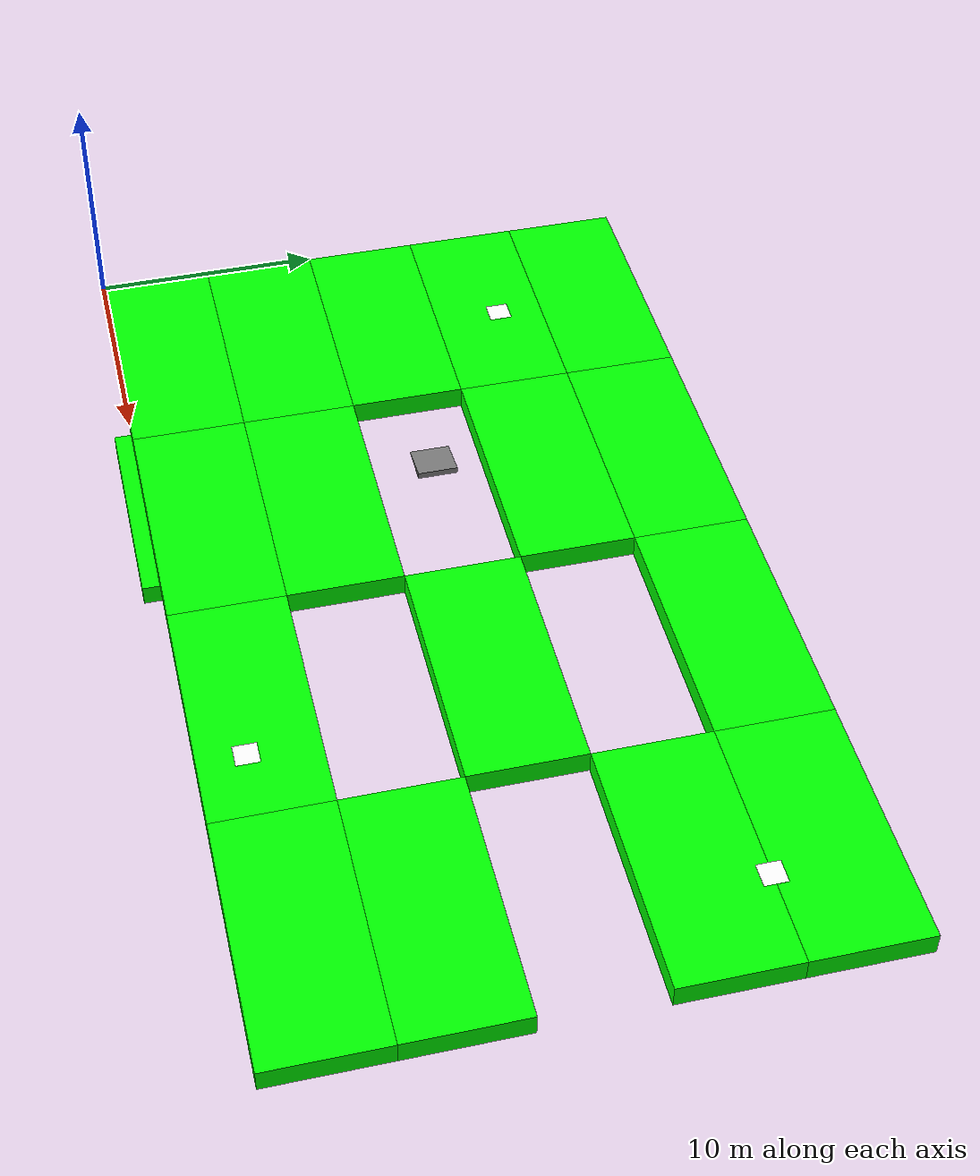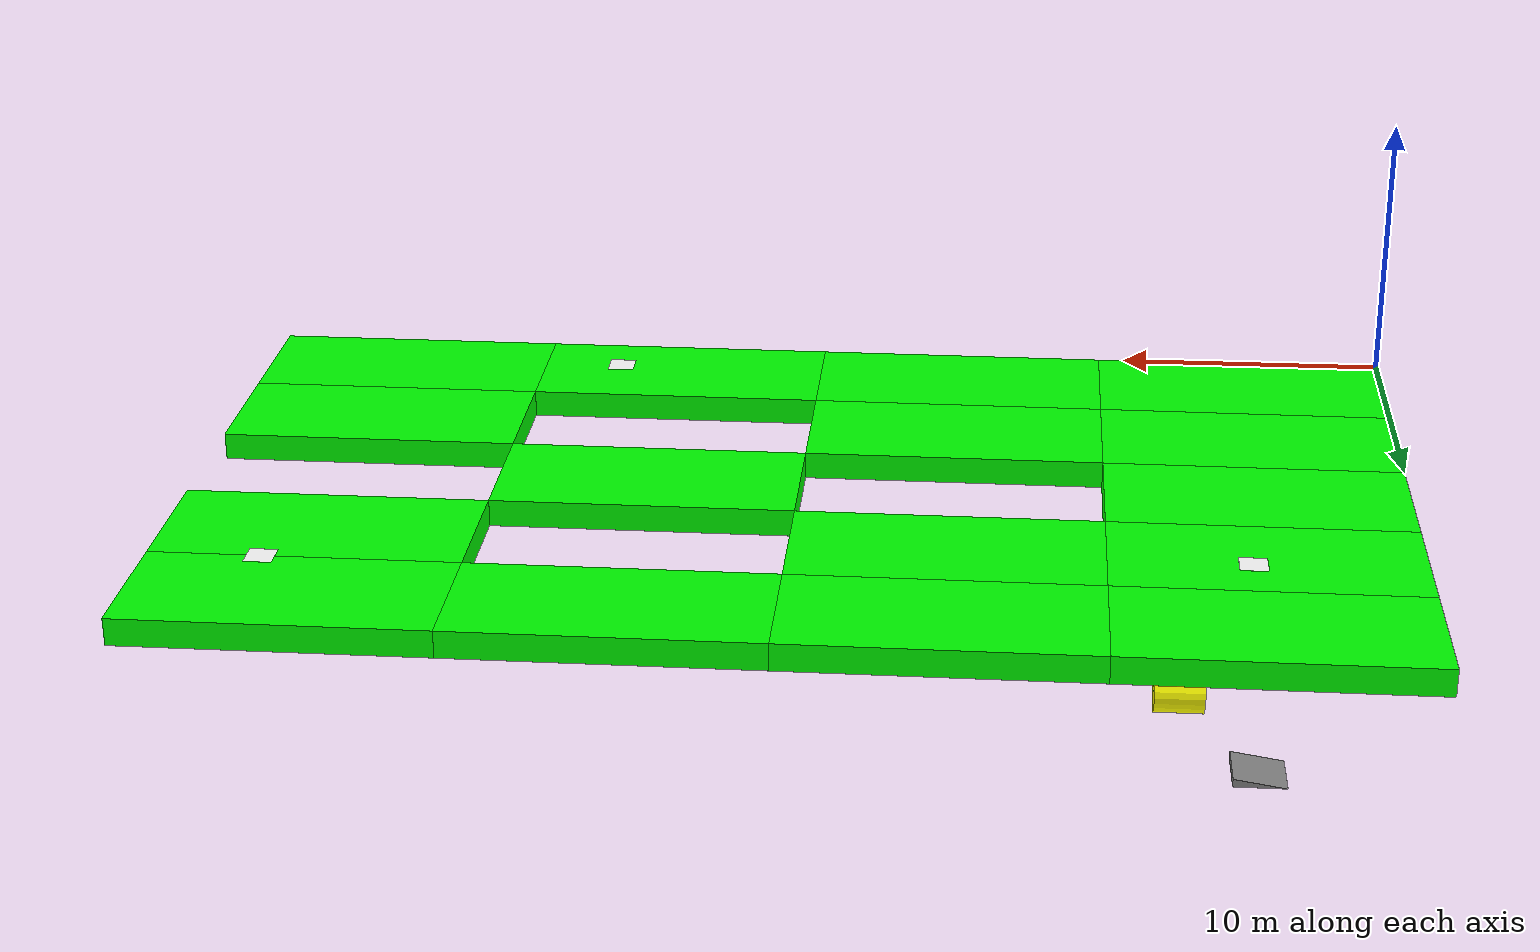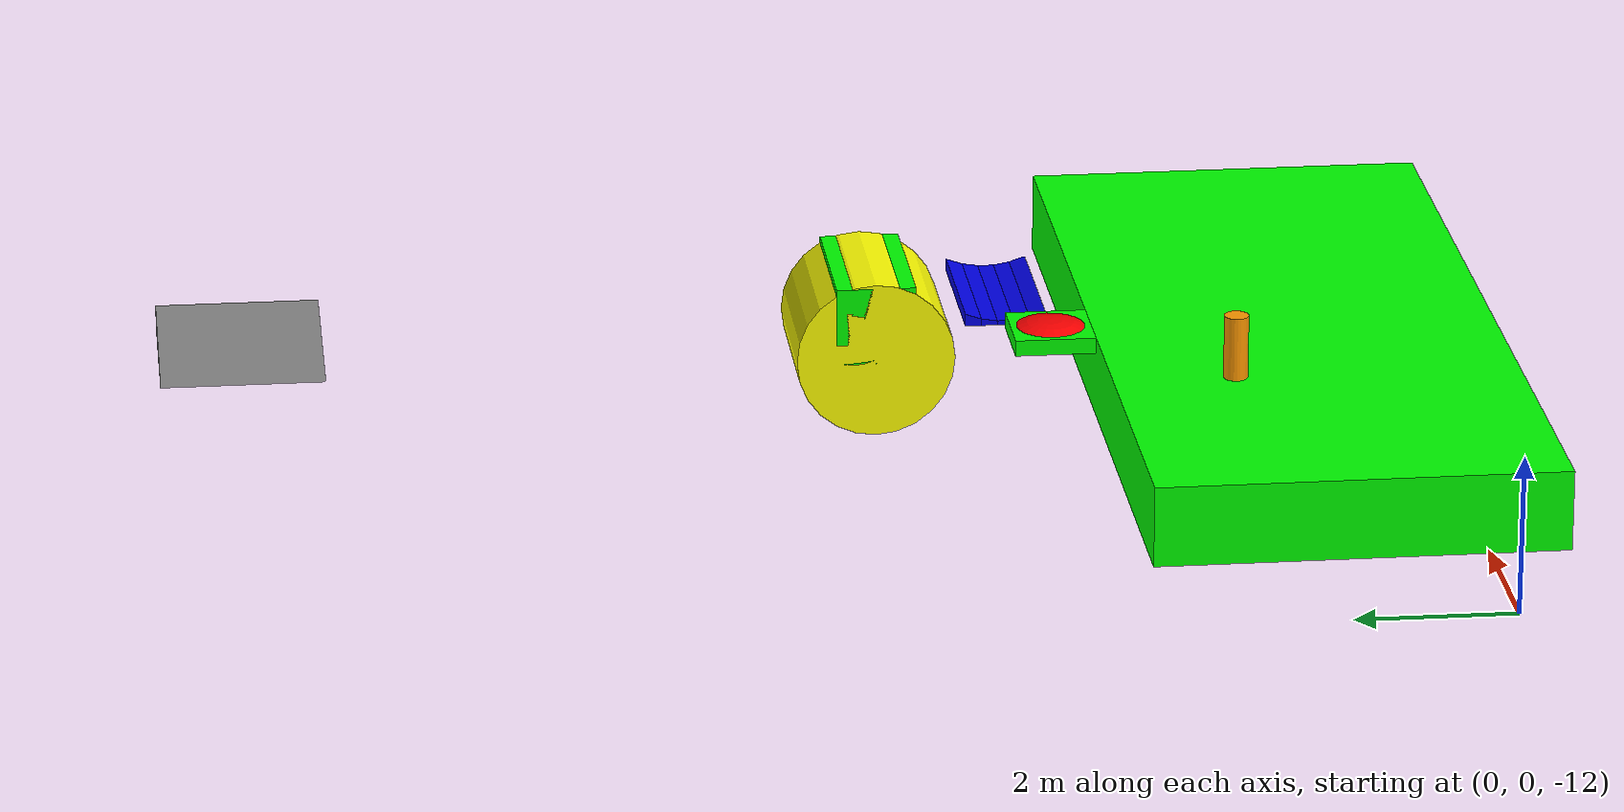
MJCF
<mujoco model="field (v2.0)">
    <compiler inertiafromgeom="true" angle="degree"/>
	<option	timestep="0.02" gravity="0 0 -9.81"/>

	<asset>
		<!--texture type ="2d" name="PixelGround" file="texture3_field.png"/-->
		<material name="MatGnd" specular="1" shininess=".3" reflectance="0" rgba="0 1 0 1" />
		<!--material name="MatGnd" specular="1" shininess=".3" reflectance="0" rgba="0 1 0 1" texture="PixelGround" /-->
		<material name="MatSpot" specular="1" shininess="0" reflectance="0.5" rgba="1 1 1 1"/>
		<material name="MatInit" rgba="0.8 0 0 1"/>

	</asset>

	<default>
		<geom contype="1" conaffinity="1"/>
		<mesh scale="1 1 1"/>
	</default>

    <worldbody>
		<camera name="overview" mode="fixed" pos="22 12.5 35"/>
		<light directional="true" cutoff="4" exponent="20" diffuse="1 1 1" specular="0 0 0" pos="0 .3 2.5" dir="0 -.3 -2.5 "/>
		<geom name="ground1" type="box" pos="5.5 2.5 -.5" size="5.5 2.5 .5" material="MatGnd"/>
		<geom name="ground2" type="box" pos="5.5 7.5 -.5" size="5.5 2.5 .5" material="MatGnd"/>
		<geom name="ground3" type="box" pos="5.5 12.5 -.5" size="5.5 2.5 .5" material="MatGnd"/>
		<geom name="ground4" type="box" pos="5.5 17.5 -.5" size="5.5 2.5 .5" material="MatGnd"/>
		<geom name="ground5" type="box" pos="5.5 22.5 -.5" size="5.5 2.5 .5" material="MatGnd"/>
		<geom name="ground6" type="box" pos="16.5 2.5 -.5" size="5.5 2.5 .5" material="MatGnd"/>
		<geom name="ground7" type="box" pos="16.5 7.5 -.5" size="5.5 2.5 .5" material="MatGnd"/>
		<geom name="ground8" type="box" pos="16.5 17.5 -.5" size="5.5 2.5 .5" material="MatGnd"/>
		<geom name="ground9" type="box" pos="16.5 22.5 -.5" size="5.5 2.5 .5" material="MatGnd"/>
		<geom name="ground10" type="box" pos="27.5 2.5 -.5" size="5.5 2.5 .5" material="MatGnd"/>
		<geom name="ground11" type="box" pos="27.5 12.5 -.5" size="5.5 2.5 .5" material="MatGnd"/>
		<geom name="ground12" type="box" pos="27.5 22.5 -.5" size="5.5 2.5 .5" material="MatGnd"/>
		<geom name="ground13" type="box" pos="38.5 2.5 -.5" size="5.5 2.5 .5" material="MatGnd"/>
		<geom name="ground14" type="box" pos="38.5 7.5 -.5" size="5.5 2.5 .5" material="MatGnd"/>
		<geom name="ground15" type="box" pos="38.5 17.5 -.5" size="5.5 2.5 .5" material="MatGnd"/>
		<geom name="ground16" type="box" pos="38.5 22.5 -.5" size="5.5 2.5 .5" material="MatGnd"/>
		<geom name="init" type="plane" pos="3 3 .001" size=".5 .5 .1" conaffinity="0" contype="0" material="MatInit"/>
		<geom name="spot-0" type="box" pos="6 18 .001" size=".5 .5 .001" material="MatSpot"/>
		<geom name="spot-1" type="box" pos="30 2 .001" size=".5 .5 .001" material="MatSpot"/>
		<geom name="spot-2" type="box" pos="40 20 .001" size=".5 .5 .001" material="MatSpot"/>
		<body name="hole_filler1" pos="0 0 -10">
			<geom type="box" pos="5 2 -0.5" size="5.5 2.5 .5" material="MatGnd"/>
		</body>
		<body name="hole_filler2" pos="0 0 -10">
			<geom type="box" pos="5 2 -0.5" size="5.5 2.5 .5" material="MatGnd"/>
		</body>
        <body name="hole_filler3" pos="0 0 -10">
			<geom type="box" pos="5 2 -0.5" size="5.5 2.5 .5" material="MatGnd"/>
		</body>
        <body name="hole_filler4" pos="0 0 -10">
			<geom type="box" pos="5 2 -0.5" size="5.5 2.5 .5" material="MatGnd"/>
		</body>
	</worldbody>
	<include file="ramp.xml"/>
	<include file="box-tile.xml"/>
	<include file="square-hole.xml"/>
	<include file="square-long-hole.xml"/>
	<include file="circular-bump.xml"/>
	<include file="long-bump.xml"/>
	<include file="post.xml"/>
</mujoco>

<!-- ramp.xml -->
<mujoco model="ramp (v0.1)">
    <compiler inertiafromgeom="true" angle="degree"/>
	<option	timestep="0.01" gravity="0 0 -9.81"/>

	<asset>
		<!--material name="MatGnd" specular="1" shininess=".3" reflectance="0" rgba="1 1 1 1" texture="PixelGround" /-->
		<!--material name="MatSpot" specular="1" shininess="0" reflectance="0.5" rgba="1 1 1 1"/-->
		<!--material name="MatInit" rgba=".8 0 0 1"/-->
		<mesh name="ramp-blender" file="ramp-blender.stl" scale="1 1 .8"/>
	</asset>

	<default>
		<geom contype="1" conaffinity="1"/>
	</default>

    <worldbody>
		<body name="ramp1" pos="5 15 -10">
			<geom name="ramp1geom" type="mesh" pos="0 0 0" mesh="ramp-blender"/>
		</body>
		<body name="ramp2" pos="5 15 -10">
			<geom name="ramp2geom" type="mesh" pos="0 0 0" mesh="ramp-blender"/>
		</body>
		<body name="ramp3" pos="5 15 -10">
			<geom name="ramp3geom" type="mesh" pos="0 0 0" mesh="ramp-blender"/>
		</body>
		<body name="ramp4" pos="5 15 -10">
			<geom name="ramp5geom" type="mesh" pos="0 0 0" mesh="ramp-blender"/>
		</body>
	</worldbody>
</mujoco>

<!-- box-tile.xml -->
<mujoco model="box tile (v0.1)">
    <compiler inertiafromgeom="true" angle="degree"/>
	<option	timestep="0.01" gravity="0 0 -9.81"/>

	<asset>
		<!--material name="MatGnd" specular="1" shininess=".3" reflectance="0" rgba="1 1 1 1" texture="PixelGround" /-->
		<!--material name="MatSpot" specular="1" shininess="0" reflectance="0.5" rgba="1 1 1 1"/-->
		<!--material name="MatInit" rgba=".8 0 0 1"/-->
	</asset>

	<default>
		<geom contype="1" conaffinity="1"/>
	</default>

    <worldbody>
		<body name="box-tile1" pos="5 5 -10">
			<geom type="box" size=".5 .5 .1" pos = "0 0 -.1" rgba="0 1 0 1" />
		</body>
		<body name="box-tile2" pos="5 5 -10">
			<geom type="box" size=".5 .5 .1" pos = "0 0 -.1" rgba="0 1 0 1" />
		</body>
		<body name="box-tile3" pos="5 5 -10">
			<geom type="box" size=".5 .5 .1" pos = "0 0 -.1" rgba="0 1 0 1" />
		</body>
		<body name="box-tile4" pos="5 5 -10">
			<geom type="box" size=".5 .5 .1" pos = "0 0 -.1" rgba="0 1 0 1" />
		</body>
		<body name="box-tile5" pos="5 5 -10">
			<geom type="box" size=".5 .5 .1" pos = "0 0 -.1" rgba="0 1 0 1" />
		</body>
		<body name="box-tile6" pos="5 5 -10">
			<geom type="box" size=".5 .5 .1" pos = "0 0 -.1" rgba="0 1 0 1" />
		</body>
		<body name="box-tile7" pos="5 5 -10">
			<geom type="box" size=".5 .5 .1" pos = "0 0 -.1" rgba="0 1 0 1" />
		</body>
		<body name="box-tile8" pos="5 5 -10">
			<geom type="box" size=".5 .5 .1" pos = "0 0 -.1" rgba="0 1 0 1" />
		</body>
		<body name="box-tile9" pos="5 5 -10">
			<geom type="box" size=".5 .5 .1" pos = "0 0 -.1" rgba="0 1 0 1" />
		</body>
		<body name="box-tile10" pos="5 5 -10">
			<geom type="box" size=".5 .5 .1" pos = "0 0 -.1" rgba="0 1 0 1" />
		</body>
		<body name="box-tile11" pos="5 5 -10">
			<geom type="box" size=".5 .5 .1" pos = "0 0 -.1" rgba="0 1 0 1" />
		</body>
		<body name="box-tile12" pos="5 5 -10">
			<geom type="box" size=".5 .5 .1" pos = "0 0 -.1" rgba="0 1 0 1" />
		</body>
		<body name="box-tile13" pos="5 5 -10">
			<geom type="box" size=".5 .5 .1" pos = "0 0 -.1" rgba="0 1 0 1" />
		</body>
		<body name="box-tile14" pos="5 5 -10">
			<geom type="box" size=".5 .5 .1" pos = "0 0 -.1" rgba="0 1 0 1" />
		</body>
		<body name="box-tile15" pos="5 5 -10">
			<geom type="box" size=".5 .5 .1" pos = "0 0 -.1" rgba="0 1 0 1" />
		</body>
		<body name="box-tile16" pos="5 5 -10">
			<geom type="box" size=".5 .5 .1" pos = "0 0 -.1" rgba="0 1 0 1" />
		</body>
		<body name="box-tile17" pos="5 5 -10">
			<geom type="box" size=".5 .5 .1" pos = "0 0 -.1" rgba="0 1 0 1" />
		</body>
		<body name="box-tile18" pos="5 5 -10">
			<geom type="box" size=".5 .5 .1" pos = "0 0 -.1" rgba="0 1 0 1" />
		</body>
		<body name="box-tile19" pos="5 5 -10">
			<geom type="box" size=".5 .5 .1" pos = "0 0 -.1" rgba="0 1 0 1" />
		</body>
		<body name="box-tile20" pos="5 5 -10">
			<geom type="box" size=".5 .5 .1" pos = "0 0 -.1" rgba="0 1 0 1" />
		</body>
		<body name="box-tile21" pos="5 5 -10">
			<geom type="box" size=".5 .5 .1" pos = "0 0 -.1" rgba="0 1 0 1" />
		</body>
		<body name="box-tile22" pos="5 5 -10">
			<geom type="box" size=".5 .5 .1" pos = "0 0 -.1" rgba="0 1 0 1" />
		</body>
		<body name="box-tile23" pos="5 5 -10">
			<geom type="box" size=".5 .5 .1" pos = "0 0 -.1" rgba="0 1 0 1" />
		</body>
		<body name="box-tile24" pos="5 5 -10">
			<geom type="box" size=".5 .5 .1" pos = "0 0 -.1" rgba="0 1 0 1" />
		</body>
		<body name="box-tile25" pos="5 5 -10">
			<geom type="box" size=".5 .5 .1" pos = "0 0 -.1" rgba="0 1 0 1" />
		</body>
		<body name="box-tile26" pos="5 5 -10">
			<geom type="box" size=".5 .5 .1" pos = "0 0 -.1" rgba="0 1 0 1" />
		</body>
		<body name="box-tile27" pos="5 5 -10">
			<geom type="box" size=".5 .5 .1" pos = "0 0 -.1" rgba="0 1 0 1" />
		</body>
		<body name="box-tile28" pos="5 5 -10">
			<geom type="box" size=".5 .5 .1" pos = "0 0 -.1" rgba="0 1 0 1" />
		</body>
		<body name="box-tile29" pos="5 5 -10">
			<geom type="box" size=".5 .5 .1" pos = "0 0 -.1" rgba="0 1 0 1" />
		</body>
		<body name="box-tile30" pos="5 5 -10">
			<geom type="box" size=".5 .5 .1" pos = "0 0 -.1" rgba="0 1 0 1" />
		</body>
		<body name="box-tile31" pos="5 5 -10">
			<geom type="box" size=".5 .5 .1" pos = "0 0 -.1" rgba="0 1 0 1" />
		</body>
		<body name="box-tile32" pos="5 5 -10">
			<geom type="box" size=".5 .5 .1" pos = "0 0 -.1" rgba="0 1 0 1" />
		</body>
		<body name="box-tile33" pos="5 5 -10">
			<geom type="box" size=".5 .5 .1" pos = "0 0 -.1" rgba="0 1 0 1" />
		</body>
		<body name="box-tile34" pos="5 5 -10">
			<geom type="box" size=".5 .5 .1" pos = "0 0 -.1" rgba="0 1 0 1" />
		</body>
		<body name="box-tile35" pos="5 5 -10">
			<geom type="box" size=".5 .5 .1" pos = "0 0 -.1" rgba="0 1 0 1" />
		</body>
		<body name="box-tile36" pos="5 5 -10">
			<geom type="box" size=".5 .5 .1" pos = "0 0 -.1" rgba="0 1 0 1" />
		</body>
		<body name="box-tile37" pos="5 5 -10">
			<geom type="box" size=".5 .5 .1" pos = "0 0 -.1" rgba="0 1 0 1" />
		</body>
		<body name="box-tile38" pos="5 5 -10">
			<geom type="box" size=".5 .5 .1" pos = "0 0 -.1" rgba="0 1 0 1" />
		</body>
		<body name="box-tile39" pos="5 5 -10">
			<geom type="box" size=".5 .5 .1" pos = "0 0 -.1" rgba="0 1 0 1" />
		</body>
		<body name="box-tile40" pos="5 5 -10">
			<geom type="box" size=".5 .5 .1" pos = "0 0 -.1" rgba="0 1 0 1" />
		</body>
	</worldbody>
</mujoco>

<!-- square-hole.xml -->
<mujoco model="square hole (v0.1)">
    <compiler inertiafromgeom="true" angle="degree"/>
	<option	timestep="0.01" gravity="0 0 -9.81"/>

	<asset>
		<!--material name="MatGnd" specular="1" shininess=".3" reflectance="0" rgba="1 1 1 1" texture="PixelGround" /-->
		<!--material name="MatSpot" specular="1" shininess="0" reflectance="0.5" rgba="1 1 1 1"/-->
		<!--material name="MatInit" rgba=".8 0 0 1"/-->
		<mesh name="part_x+1" file="square_hole_x+1.stl" scale=".5 .5 .65"/>
		<mesh name="part_x+2" file="square_hole_x+2.stl" scale=".5 .5 .65"/>
		<mesh name="part_y+1" file="square_hole_y+1.stl" scale=".5 .5 .65"/>
		<mesh name="part_y+2" file="square_hole_y+2.stl" scale=".5 .5 .65"/>
		<mesh name="part_x-1" file="square_hole_x-1.stl" scale=".5 .5 .65"/>
		<mesh name="part_x-2" file="square_hole_x-2.stl" scale=".5 .5 .65"/>
		<mesh name="part_y-1" file="square_hole_y-1.stl" scale=".5 .5 .65"/>
		<mesh name="part_y-2" file="square_hole_y-2.stl" scale=".5 .5 .65"/>
		<mesh name="part_center" file="square_hole_center.stl" scale=".5 .5 .65"/>
	</asset>

	<default>
		<geom contype="1" conaffinity="1"/>
	</default>

    <worldbody>
		<body name="square-hole1" pos="3 .5 -10">
			<geom type="mesh" mesh="part_x+1" rgba=".259 .145 .094 1"/>
			<geom type="mesh" mesh="part_x+2" rgba=".259 .145 .094 1"/>
			<geom type="mesh" mesh="part_y+1" rgba=".259 .145 .094 1"/>
			<geom type="mesh" mesh="part_y+2" rgba=".259 .145 .094 1"/>
			<geom type="mesh" mesh="part_x-1" rgba=".259 .145 .094 1"/>
			<geom type="mesh" mesh="part_x-2" rgba=".259 .145 .094 1"/>
			<geom type="mesh" mesh="part_y-1" rgba=".259 .145 .094 1"/>
			<geom type="mesh" mesh="part_y-2" rgba=".259 .145 .094 1"/>
			<geom type="mesh" mesh="part_center" rgba=".259 .145 .094 1"/>
		</body>
		<body name="square-hole2" pos="3 .5 -10">
			<geom type="mesh" mesh="part_x+1" rgba=".259 .145 .094 1"/>
			<geom type="mesh" mesh="part_x+2" rgba=".259 .145 .094 1"/>
			<geom type="mesh" mesh="part_y+1" rgba=".259 .145 .094 1"/>
			<geom type="mesh" mesh="part_y+2" rgba=".259 .145 .094 1"/>
			<geom type="mesh" mesh="part_x-1" rgba=".259 .145 .094 1"/>
			<geom type="mesh" mesh="part_x-2" rgba=".259 .145 .094 1"/>
			<geom type="mesh" mesh="part_y-1" rgba=".259 .145 .094 1"/>
			<geom type="mesh" mesh="part_y-2" rgba=".259 .145 .094 1"/>
			<geom type="mesh" mesh="part_center" rgba=".259 .145 .094 1"/>
		</body>
		<body name="square-hole3" pos="3 .5 -10">
			<geom type="mesh" mesh="part_x+1" rgba=".259 .145 .094 1"/>
			<geom type="mesh" mesh="part_x+2" rgba=".259 .145 .094 1"/>
			<geom type="mesh" mesh="part_y+1" rgba=".259 .145 .094 1"/>
			<geom type="mesh" mesh="part_y+2" rgba=".259 .145 .094 1"/>
			<geom type="mesh" mesh="part_x-1" rgba=".259 .145 .094 1"/>
			<geom type="mesh" mesh="part_x-2" rgba=".259 .145 .094 1"/>
			<geom type="mesh" mesh="part_y-1" rgba=".259 .145 .094 1"/>
			<geom type="mesh" mesh="part_y-2" rgba=".259 .145 .094 1"/>
			<geom type="mesh" mesh="part_center" rgba=".259 .145 .094 1"/>
		</body>
		<body name="square-hole4" pos="3 .5 -10">
			<geom type="mesh" mesh="part_x+1" rgba=".259 .145 .094 1"/>
			<geom type="mesh" mesh="part_x+2" rgba=".259 .145 .094 1"/>
			<geom type="mesh" mesh="part_y+1" rgba=".259 .145 .094 1"/>
			<geom type="mesh" mesh="part_y+2" rgba=".259 .145 .094 1"/>
			<geom type="mesh" mesh="part_x-1" rgba=".259 .145 .094 1"/>
			<geom type="mesh" mesh="part_x-2" rgba=".259 .145 .094 1"/>
			<geom type="mesh" mesh="part_y-1" rgba=".259 .145 .094 1"/>
			<geom type="mesh" mesh="part_y-2" rgba=".259 .145 .094 1"/>
			<geom type="mesh" mesh="part_center" rgba=".259 .145 .094 1"/>
		</body>
		<body name="square-hole5" pos="3 .5 -10">
			<geom type="mesh" mesh="part_x+1" rgba=".259 .145 .094 1"/>
			<geom type="mesh" mesh="part_x+2" rgba=".259 .145 .094 1"/>
			<geom type="mesh" mesh="part_y+1" rgba=".259 .145 .094 1"/>
			<geom type="mesh" mesh="part_y+2" rgba=".259 .145 .094 1"/>
			<geom type="mesh" mesh="part_x-1" rgba=".259 .145 .094 1"/>
			<geom type="mesh" mesh="part_x-2" rgba=".259 .145 .094 1"/>
			<geom type="mesh" mesh="part_y-1" rgba=".259 .145 .094 1"/>
			<geom type="mesh" mesh="part_y-2" rgba=".259 .145 .094 1"/>
			<geom type="mesh" mesh="part_center" rgba=".259 .145 .094 1"/>
		</body>
		<body name="square-hole6" pos="3 .5 -10">
			<geom type="mesh" mesh="part_x+1" rgba=".259 .145 .094 1"/>
			<geom type="mesh" mesh="part_x+2" rgba=".259 .145 .094 1"/>
			<geom type="mesh" mesh="part_y+1" rgba=".259 .145 .094 1"/>
			<geom type="mesh" mesh="part_y+2" rgba=".259 .145 .094 1"/>
			<geom type="mesh" mesh="part_x-1" rgba=".259 .145 .094 1"/>
			<geom type="mesh" mesh="part_x-2" rgba=".259 .145 .094 1"/>
			<geom type="mesh" mesh="part_y-1" rgba=".259 .145 .094 1"/>
			<geom type="mesh" mesh="part_y-2" rgba=".259 .145 .094 1"/>
			<geom type="mesh" mesh="part_center" rgba=".259 .145 .094 1"/>
		</body>
		<body name="square-hole7" pos="3 .5 -10">
			<geom type="mesh" mesh="part_x+1" rgba=".259 .145 .094 1"/>
			<geom type="mesh" mesh="part_x+2" rgba=".259 .145 .094 1"/>
			<geom type="mesh" mesh="part_y+1" rgba=".259 .145 .094 1"/>
			<geom type="mesh" mesh="part_y+2" rgba=".259 .145 .094 1"/>
			<geom type="mesh" mesh="part_x-1" rgba=".259 .145 .094 1"/>
			<geom type="mesh" mesh="part_x-2" rgba=".259 .145 .094 1"/>
			<geom type="mesh" mesh="part_y-1" rgba=".259 .145 .094 1"/>
			<geom type="mesh" mesh="part_y-2" rgba=".259 .145 .094 1"/>
			<geom type="mesh" mesh="part_center" rgba=".259 .145 .094 1"/>
		</body>
		<body name="square-hole8" pos="3 .5 -10">
			<geom type="mesh" mesh="part_x+1" rgba=".259 .145 .094 1"/>
			<geom type="mesh" mesh="part_x+2" rgba=".259 .145 .094 1"/>
			<geom type="mesh" mesh="part_y+1" rgba=".259 .145 .094 1"/>
			<geom type="mesh" mesh="part_y+2" rgba=".259 .145 .094 1"/>
			<geom type="mesh" mesh="part_x-1" rgba=".259 .145 .094 1"/>
			<geom type="mesh" mesh="part_x-2" rgba=".259 .145 .094 1"/>
			<geom type="mesh" mesh="part_y-1" rgba=".259 .145 .094 1"/>
			<geom type="mesh" mesh="part_y-2" rgba=".259 .145 .094 1"/>
			<geom type="mesh" mesh="part_center" rgba=".259 .145 .094 1"/>
		</body>
		<body name="square-hole9" pos="3 .5 -10">
			<geom type="mesh" mesh="part_x+1" rgba=".259 .145 .094 1"/>
			<geom type="mesh" mesh="part_x+2" rgba=".259 .145 .094 1"/>
			<geom type="mesh" mesh="part_y+1" rgba=".259 .145 .094 1"/>
			<geom type="mesh" mesh="part_y+2" rgba=".259 .145 .094 1"/>
			<geom type="mesh" mesh="part_x-1" rgba=".259 .145 .094 1"/>
			<geom type="mesh" mesh="part_x-2" rgba=".259 .145 .094 1"/>
			<geom type="mesh" mesh="part_y-1" rgba=".259 .145 .094 1"/>
			<geom type="mesh" mesh="part_y-2" rgba=".259 .145 .094 1"/>
			<geom type="mesh" mesh="part_center" rgba=".259 .145 .094 1"/>
		</body>
		<body name="square-hole10" pos="3 .5 -10">
			<geom type="mesh" mesh="part_x+1" rgba=".259 .145 .094 1"/>
			<geom type="mesh" mesh="part_x+2" rgba=".259 .145 .094 1"/>
			<geom type="mesh" mesh="part_y+1" rgba=".259 .145 .094 1"/>
			<geom type="mesh" mesh="part_y+2" rgba=".259 .145 .094 1"/>
			<geom type="mesh" mesh="part_x-1" rgba=".259 .145 .094 1"/>
			<geom type="mesh" mesh="part_x-2" rgba=".259 .145 .094 1"/>
			<geom type="mesh" mesh="part_y-1" rgba=".259 .145 .094 1"/>
			<geom type="mesh" mesh="part_y-2" rgba=".259 .145 .094 1"/>
			<geom type="mesh" mesh="part_center" rgba=".259 .145 .094 1"/>
		</body>
		<body name="square-hole11" pos="3 .5 -10">
			<geom type="mesh" mesh="part_x+1" rgba=".259 .145 .094 1"/>
			<geom type="mesh" mesh="part_x+2" rgba=".259 .145 .094 1"/>
			<geom type="mesh" mesh="part_y+1" rgba=".259 .145 .094 1"/>
			<geom type="mesh" mesh="part_y+2" rgba=".259 .145 .094 1"/>
			<geom type="mesh" mesh="part_x-1" rgba=".259 .145 .094 1"/>
			<geom type="mesh" mesh="part_x-2" rgba=".259 .145 .094 1"/>
			<geom type="mesh" mesh="part_y-1" rgba=".259 .145 .094 1"/>
			<geom type="mesh" mesh="part_y-2" rgba=".259 .145 .094 1"/>
			<geom type="mesh" mesh="part_center" rgba=".259 .145 .094 1"/>
		</body>
		<body name="square-hole12" pos="3 .5 -10">
			<geom type="mesh" mesh="part_x+1" rgba=".259 .145 .094 1"/>
			<geom type="mesh" mesh="part_x+2" rgba=".259 .145 .094 1"/>
			<geom type="mesh" mesh="part_y+1" rgba=".259 .145 .094 1"/>
			<geom type="mesh" mesh="part_y+2" rgba=".259 .145 .094 1"/>
			<geom type="mesh" mesh="part_x-1" rgba=".259 .145 .094 1"/>
			<geom type="mesh" mesh="part_x-2" rgba=".259 .145 .094 1"/>
			<geom type="mesh" mesh="part_y-1" rgba=".259 .145 .094 1"/>
			<geom type="mesh" mesh="part_y-2" rgba=".259 .145 .094 1"/>
			<geom type="mesh" mesh="part_center" rgba=".259 .145 .094 1"/>
		</body>
		<body name="square-hole13" pos="3 .5 -10">
			<geom type="mesh" mesh="part_x+1" rgba=".259 .145 .094 1"/>
			<geom type="mesh" mesh="part_x+2" rgba=".259 .145 .094 1"/>
			<geom type="mesh" mesh="part_y+1" rgba=".259 .145 .094 1"/>
			<geom type="mesh" mesh="part_y+2" rgba=".259 .145 .094 1"/>
			<geom type="mesh" mesh="part_x-1" rgba=".259 .145 .094 1"/>
			<geom type="mesh" mesh="part_x-2" rgba=".259 .145 .094 1"/>
			<geom type="mesh" mesh="part_y-1" rgba=".259 .145 .094 1"/>
			<geom type="mesh" mesh="part_y-2" rgba=".259 .145 .094 1"/>
			<geom type="mesh" mesh="part_center" rgba=".259 .145 .094 1"/>
		</body>
		<body name="square-hole14" pos="3 .5 -10">
			<geom type="mesh" mesh="part_x+1" rgba=".259 .145 .094 1"/>
			<geom type="mesh" mesh="part_x+2" rgba=".259 .145 .094 1"/>
			<geom type="mesh" mesh="part_y+1" rgba=".259 .145 .094 1"/>
			<geom type="mesh" mesh="part_y+2" rgba=".259 .145 .094 1"/>
			<geom type="mesh" mesh="part_x-1" rgba=".259 .145 .094 1"/>
			<geom type="mesh" mesh="part_x-2" rgba=".259 .145 .094 1"/>
			<geom type="mesh" mesh="part_y-1" rgba=".259 .145 .094 1"/>
			<geom type="mesh" mesh="part_y-2" rgba=".259 .145 .094 1"/>
			<geom type="mesh" mesh="part_center" rgba=".259 .145 .094 1"/>
		</body>
		<body name="square-hole15" pos="3 .5 -10">
			<geom type="mesh" mesh="part_x+1" rgba=".259 .145 .094 1"/>
			<geom type="mesh" mesh="part_x+2" rgba=".259 .145 .094 1"/>
			<geom type="mesh" mesh="part_y+1" rgba=".259 .145 .094 1"/>
			<geom type="mesh" mesh="part_y+2" rgba=".259 .145 .094 1"/>
			<geom type="mesh" mesh="part_x-1" rgba=".259 .145 .094 1"/>
			<geom type="mesh" mesh="part_x-2" rgba=".259 .145 .094 1"/>
			<geom type="mesh" mesh="part_y-1" rgba=".259 .145 .094 1"/>
			<geom type="mesh" mesh="part_y-2" rgba=".259 .145 .094 1"/>
			<geom type="mesh" mesh="part_center" rgba=".259 .145 .094 1"/>
		</body>
        <body name="square-hole16" pos="3 .5 -10">
			<geom type="mesh" mesh="part_x+1" rgba=".259 .145 .094 1"/>
			<geom type="mesh" mesh="part_x+2" rgba=".259 .145 .094 1"/>
			<geom type="mesh" mesh="part_y+1" rgba=".259 .145 .094 1"/>
			<geom type="mesh" mesh="part_y+2" rgba=".259 .145 .094 1"/>
			<geom type="mesh" mesh="part_x-1" rgba=".259 .145 .094 1"/>
			<geom type="mesh" mesh="part_x-2" rgba=".259 .145 .094 1"/>
			<geom type="mesh" mesh="part_y-1" rgba=".259 .145 .094 1"/>
			<geom type="mesh" mesh="part_y-2" rgba=".259 .145 .094 1"/>
			<geom type="mesh" mesh="part_center" rgba=".259 .145 .094 1"/>
		</body>
        <body name="square-hole17" pos="3 .5 -10">
			<geom type="mesh" mesh="part_x+1" rgba=".259 .145 .094 1"/>
			<geom type="mesh" mesh="part_x+2" rgba=".259 .145 .094 1"/>
			<geom type="mesh" mesh="part_y+1" rgba=".259 .145 .094 1"/>
			<geom type="mesh" mesh="part_y+2" rgba=".259 .145 .094 1"/>
			<geom type="mesh" mesh="part_x-1" rgba=".259 .145 .094 1"/>
			<geom type="mesh" mesh="part_x-2" rgba=".259 .145 .094 1"/>
			<geom type="mesh" mesh="part_y-1" rgba=".259 .145 .094 1"/>
			<geom type="mesh" mesh="part_y-2" rgba=".259 .145 .094 1"/>
			<geom type="mesh" mesh="part_center" rgba=".259 .145 .094 1"/>
		</body>
        <body name="square-hole18" pos="3 .5 -10">
			<geom type="mesh" mesh="part_x+1" rgba=".259 .145 .094 1"/>
			<geom type="mesh" mesh="part_x+2" rgba=".259 .145 .094 1"/>
			<geom type="mesh" mesh="part_y+1" rgba=".259 .145 .094 1"/>
			<geom type="mesh" mesh="part_y+2" rgba=".259 .145 .094 1"/>
			<geom type="mesh" mesh="part_x-1" rgba=".259 .145 .094 1"/>
			<geom type="mesh" mesh="part_x-2" rgba=".259 .145 .094 1"/>
			<geom type="mesh" mesh="part_y-1" rgba=".259 .145 .094 1"/>
			<geom type="mesh" mesh="part_y-2" rgba=".259 .145 .094 1"/>
			<geom type="mesh" mesh="part_center" rgba=".259 .145 .094 1"/>
		</body>
        <body name="square-hole19" pos="3 .5 -10">
			<geom type="mesh" mesh="part_x+1" rgba=".259 .145 .094 1"/>
			<geom type="mesh" mesh="part_x+2" rgba=".259 .145 .094 1"/>
			<geom type="mesh" mesh="part_y+1" rgba=".259 .145 .094 1"/>
			<geom type="mesh" mesh="part_y+2" rgba=".259 .145 .094 1"/>
			<geom type="mesh" mesh="part_x-1" rgba=".259 .145 .094 1"/>
			<geom type="mesh" mesh="part_x-2" rgba=".259 .145 .094 1"/>
			<geom type="mesh" mesh="part_y-1" rgba=".259 .145 .094 1"/>
			<geom type="mesh" mesh="part_y-2" rgba=".259 .145 .094 1"/>
			<geom type="mesh" mesh="part_center" rgba=".259 .145 .094 1"/>
		</body>
        <body name="square-hole20" pos="3 .5 -10">
			<geom type="mesh" mesh="part_x+1" rgba=".259 .145 .094 1"/>
			<geom type="mesh" mesh="part_x+2" rgba=".259 .145 .094 1"/>
			<geom type="mesh" mesh="part_y+1" rgba=".259 .145 .094 1"/>
			<geom type="mesh" mesh="part_y+2" rgba=".259 .145 .094 1"/>
			<geom type="mesh" mesh="part_x-1" rgba=".259 .145 .094 1"/>
			<geom type="mesh" mesh="part_x-2" rgba=".259 .145 .094 1"/>
			<geom type="mesh" mesh="part_y-1" rgba=".259 .145 .094 1"/>
			<geom type="mesh" mesh="part_y-2" rgba=".259 .145 .094 1"/>
			<geom type="mesh" mesh="part_center" rgba=".259 .145 .094 1"/>
		</body>
        <body name="square-hole21" pos="3 .5 -10">
			<geom type="mesh" mesh="part_x+1" rgba=".259 .145 .094 1"/>
			<geom type="mesh" mesh="part_x+2" rgba=".259 .145 .094 1"/>
			<geom type="mesh" mesh="part_y+1" rgba=".259 .145 .094 1"/>
			<geom type="mesh" mesh="part_y+2" rgba=".259 .145 .094 1"/>
			<geom type="mesh" mesh="part_x-1" rgba=".259 .145 .094 1"/>
			<geom type="mesh" mesh="part_x-2" rgba=".259 .145 .094 1"/>
			<geom type="mesh" mesh="part_y-1" rgba=".259 .145 .094 1"/>
			<geom type="mesh" mesh="part_y-2" rgba=".259 .145 .094 1"/>
			<geom type="mesh" mesh="part_center" rgba=".259 .145 .094 1"/>
		</body>
        <body name="square-hole22" pos="3 .5 -10">
			<geom type="mesh" mesh="part_x+1" rgba=".259 .145 .094 1"/>
			<geom type="mesh" mesh="part_x+2" rgba=".259 .145 .094 1"/>
			<geom type="mesh" mesh="part_y+1" rgba=".259 .145 .094 1"/>
			<geom type="mesh" mesh="part_y+2" rgba=".259 .145 .094 1"/>
			<geom type="mesh" mesh="part_x-1" rgba=".259 .145 .094 1"/>
			<geom type="mesh" mesh="part_x-2" rgba=".259 .145 .094 1"/>
			<geom type="mesh" mesh="part_y-1" rgba=".259 .145 .094 1"/>
			<geom type="mesh" mesh="part_y-2" rgba=".259 .145 .094 1"/>
			<geom type="mesh" mesh="part_center" rgba=".259 .145 .094 1"/>
		</body>
        <body name="square-hole23" pos="3 .5 -10">
			<geom type="mesh" mesh="part_x+1" rgba=".259 .145 .094 1"/>
			<geom type="mesh" mesh="part_x+2" rgba=".259 .145 .094 1"/>
			<geom type="mesh" mesh="part_y+1" rgba=".259 .145 .094 1"/>
			<geom type="mesh" mesh="part_y+2" rgba=".259 .145 .094 1"/>
			<geom type="mesh" mesh="part_x-1" rgba=".259 .145 .094 1"/>
			<geom type="mesh" mesh="part_x-2" rgba=".259 .145 .094 1"/>
			<geom type="mesh" mesh="part_y-1" rgba=".259 .145 .094 1"/>
			<geom type="mesh" mesh="part_y-2" rgba=".259 .145 .094 1"/>
			<geom type="mesh" mesh="part_center" rgba=".259 .145 .094 1"/>
		</body>
        <body name="square-hole24" pos="3 .5 -10">
			<geom type="mesh" mesh="part_x+1" rgba=".259 .145 .094 1"/>
			<geom type="mesh" mesh="part_x+2" rgba=".259 .145 .094 1"/>
			<geom type="mesh" mesh="part_y+1" rgba=".259 .145 .094 1"/>
			<geom type="mesh" mesh="part_y+2" rgba=".259 .145 .094 1"/>
			<geom type="mesh" mesh="part_x-1" rgba=".259 .145 .094 1"/>
			<geom type="mesh" mesh="part_x-2" rgba=".259 .145 .094 1"/>
			<geom type="mesh" mesh="part_y-1" rgba=".259 .145 .094 1"/>
			<geom type="mesh" mesh="part_y-2" rgba=".259 .145 .094 1"/>
			<geom type="mesh" mesh="part_center" rgba=".259 .145 .094 1"/>
		</body>
        <body name="square-hole25" pos="3 .5 -10">
			<geom type="mesh" mesh="part_x+1" rgba=".259 .145 .094 1"/>
			<geom type="mesh" mesh="part_x+2" rgba=".259 .145 .094 1"/>
			<geom type="mesh" mesh="part_y+1" rgba=".259 .145 .094 1"/>
			<geom type="mesh" mesh="part_y+2" rgba=".259 .145 .094 1"/>
			<geom type="mesh" mesh="part_x-1" rgba=".259 .145 .094 1"/>
			<geom type="mesh" mesh="part_x-2" rgba=".259 .145 .094 1"/>
			<geom type="mesh" mesh="part_y-1" rgba=".259 .145 .094 1"/>
			<geom type="mesh" mesh="part_y-2" rgba=".259 .145 .094 1"/>
			<geom type="mesh" mesh="part_center" rgba=".259 .145 .094 1"/>
		</body>
        <body name="square-hole26" pos="3 .5 -10">
			<geom type="mesh" mesh="part_x+1" rgba=".259 .145 .094 1"/>
			<geom type="mesh" mesh="part_x+2" rgba=".259 .145 .094 1"/>
			<geom type="mesh" mesh="part_y+1" rgba=".259 .145 .094 1"/>
			<geom type="mesh" mesh="part_y+2" rgba=".259 .145 .094 1"/>
			<geom type="mesh" mesh="part_x-1" rgba=".259 .145 .094 1"/>
			<geom type="mesh" mesh="part_x-2" rgba=".259 .145 .094 1"/>
			<geom type="mesh" mesh="part_y-1" rgba=".259 .145 .094 1"/>
			<geom type="mesh" mesh="part_y-2" rgba=".259 .145 .094 1"/>
			<geom type="mesh" mesh="part_center" rgba=".259 .145 .094 1"/>
		</body>
        <body name="square-hole27" pos="3 .5 -10">
			<geom type="mesh" mesh="part_x+1" rgba=".259 .145 .094 1"/>
			<geom type="mesh" mesh="part_x+2" rgba=".259 .145 .094 1"/>
			<geom type="mesh" mesh="part_y+1" rgba=".259 .145 .094 1"/>
			<geom type="mesh" mesh="part_y+2" rgba=".259 .145 .094 1"/>
			<geom type="mesh" mesh="part_x-1" rgba=".259 .145 .094 1"/>
			<geom type="mesh" mesh="part_x-2" rgba=".259 .145 .094 1"/>
			<geom type="mesh" mesh="part_y-1" rgba=".259 .145 .094 1"/>
			<geom type="mesh" mesh="part_y-2" rgba=".259 .145 .094 1"/>
			<geom type="mesh" mesh="part_center" rgba=".259 .145 .094 1"/>
		</body>
        <body name="square-hole28" pos="3 .5 -10">
			<geom type="mesh" mesh="part_x+1" rgba=".259 .145 .094 1"/>
			<geom type="mesh" mesh="part_x+2" rgba=".259 .145 .094 1"/>
			<geom type="mesh" mesh="part_y+1" rgba=".259 .145 .094 1"/>
			<geom type="mesh" mesh="part_y+2" rgba=".259 .145 .094 1"/>
			<geom type="mesh" mesh="part_x-1" rgba=".259 .145 .094 1"/>
			<geom type="mesh" mesh="part_x-2" rgba=".259 .145 .094 1"/>
			<geom type="mesh" mesh="part_y-1" rgba=".259 .145 .094 1"/>
			<geom type="mesh" mesh="part_y-2" rgba=".259 .145 .094 1"/>
			<geom type="mesh" mesh="part_center" rgba=".259 .145 .094 1"/>
		</body>
        <body name="square-hole29" pos="3 .5 -10">
			<geom type="mesh" mesh="part_x+1" rgba=".259 .145 .094 1"/>
			<geom type="mesh" mesh="part_x+2" rgba=".259 .145 .094 1"/>
			<geom type="mesh" mesh="part_y+1" rgba=".259 .145 .094 1"/>
			<geom type="mesh" mesh="part_y+2" rgba=".259 .145 .094 1"/>
			<geom type="mesh" mesh="part_x-1" rgba=".259 .145 .094 1"/>
			<geom type="mesh" mesh="part_x-2" rgba=".259 .145 .094 1"/>
			<geom type="mesh" mesh="part_y-1" rgba=".259 .145 .094 1"/>
			<geom type="mesh" mesh="part_y-2" rgba=".259 .145 .094 1"/>
			<geom type="mesh" mesh="part_center" rgba=".259 .145 .094 1"/>
		</body>
        <body name="square-hole30" pos="3 .5 -10">
			<geom type="mesh" mesh="part_x+1" rgba=".259 .145 .094 1"/>
			<geom type="mesh" mesh="part_x+2" rgba=".259 .145 .094 1"/>
			<geom type="mesh" mesh="part_y+1" rgba=".259 .145 .094 1"/>
			<geom type="mesh" mesh="part_y+2" rgba=".259 .145 .094 1"/>
			<geom type="mesh" mesh="part_x-1" rgba=".259 .145 .094 1"/>
			<geom type="mesh" mesh="part_x-2" rgba=".259 .145 .094 1"/>
			<geom type="mesh" mesh="part_y-1" rgba=".259 .145 .094 1"/>
			<geom type="mesh" mesh="part_y-2" rgba=".259 .145 .094 1"/>
			<geom type="mesh" mesh="part_center" rgba=".259 .145 .094 1"/>
		</body>
        <body name="square-hole31" pos="3 .5 -10">
			<geom type="mesh" mesh="part_x+1" rgba=".259 .145 .094 1"/>
			<geom type="mesh" mesh="part_x+2" rgba=".259 .145 .094 1"/>
			<geom type="mesh" mesh="part_y+1" rgba=".259 .145 .094 1"/>
			<geom type="mesh" mesh="part_y+2" rgba=".259 .145 .094 1"/>
			<geom type="mesh" mesh="part_x-1" rgba=".259 .145 .094 1"/>
			<geom type="mesh" mesh="part_x-2" rgba=".259 .145 .094 1"/>
			<geom type="mesh" mesh="part_y-1" rgba=".259 .145 .094 1"/>
			<geom type="mesh" mesh="part_y-2" rgba=".259 .145 .094 1"/>
			<geom type="mesh" mesh="part_center" rgba=".259 .145 .094 1"/>
		</body>
        <body name="square-hole32" pos="3 .5 -10">
			<geom type="mesh" mesh="part_x+1" rgba=".259 .145 .094 1"/>
			<geom type="mesh" mesh="part_x+2" rgba=".259 .145 .094 1"/>
			<geom type="mesh" mesh="part_y+1" rgba=".259 .145 .094 1"/>
			<geom type="mesh" mesh="part_y+2" rgba=".259 .145 .094 1"/>
			<geom type="mesh" mesh="part_x-1" rgba=".259 .145 .094 1"/>
			<geom type="mesh" mesh="part_x-2" rgba=".259 .145 .094 1"/>
			<geom type="mesh" mesh="part_y-1" rgba=".259 .145 .094 1"/>
			<geom type="mesh" mesh="part_y-2" rgba=".259 .145 .094 1"/>
			<geom type="mesh" mesh="part_center" rgba=".259 .145 .094 1"/>
		</body>
        <body name="square-hole33" pos="3 .5 -10">
			<geom type="mesh" mesh="part_x+1" rgba=".259 .145 .094 1"/>
			<geom type="mesh" mesh="part_x+2" rgba=".259 .145 .094 1"/>
			<geom type="mesh" mesh="part_y+1" rgba=".259 .145 .094 1"/>
			<geom type="mesh" mesh="part_y+2" rgba=".259 .145 .094 1"/>
			<geom type="mesh" mesh="part_x-1" rgba=".259 .145 .094 1"/>
			<geom type="mesh" mesh="part_x-2" rgba=".259 .145 .094 1"/>
			<geom type="mesh" mesh="part_y-1" rgba=".259 .145 .094 1"/>
			<geom type="mesh" mesh="part_y-2" rgba=".259 .145 .094 1"/>
			<geom type="mesh" mesh="part_center" rgba=".259 .145 .094 1"/>
		</body>
        <body name="square-hole34" pos="3 .5 -10">
			<geom type="mesh" mesh="part_x+1" rgba=".259 .145 .094 1"/>
			<geom type="mesh" mesh="part_x+2" rgba=".259 .145 .094 1"/>
			<geom type="mesh" mesh="part_y+1" rgba=".259 .145 .094 1"/>
			<geom type="mesh" mesh="part_y+2" rgba=".259 .145 .094 1"/>
			<geom type="mesh" mesh="part_x-1" rgba=".259 .145 .094 1"/>
			<geom type="mesh" mesh="part_x-2" rgba=".259 .145 .094 1"/>
			<geom type="mesh" mesh="part_y-1" rgba=".259 .145 .094 1"/>
			<geom type="mesh" mesh="part_y-2" rgba=".259 .145 .094 1"/>
			<geom type="mesh" mesh="part_center" rgba=".259 .145 .094 1"/>
		</body>
        <body name="square-hole35" pos="3 .5 -10">
			<geom type="mesh" mesh="part_x+1" rgba=".259 .145 .094 1"/>
			<geom type="mesh" mesh="part_x+2" rgba=".259 .145 .094 1"/>
			<geom type="mesh" mesh="part_y+1" rgba=".259 .145 .094 1"/>
			<geom type="mesh" mesh="part_y+2" rgba=".259 .145 .094 1"/>
			<geom type="mesh" mesh="part_x-1" rgba=".259 .145 .094 1"/>
			<geom type="mesh" mesh="part_x-2" rgba=".259 .145 .094 1"/>
			<geom type="mesh" mesh="part_y-1" rgba=".259 .145 .094 1"/>
			<geom type="mesh" mesh="part_y-2" rgba=".259 .145 .094 1"/>
			<geom type="mesh" mesh="part_center" rgba=".259 .145 .094 1"/>
		</body>
        <body name="square-hole36" pos="3 .5 -10">
			<geom type="mesh" mesh="part_x+1" rgba=".259 .145 .094 1"/>
			<geom type="mesh" mesh="part_x+2" rgba=".259 .145 .094 1"/>
			<geom type="mesh" mesh="part_y+1" rgba=".259 .145 .094 1"/>
			<geom type="mesh" mesh="part_y+2" rgba=".259 .145 .094 1"/>
			<geom type="mesh" mesh="part_x-1" rgba=".259 .145 .094 1"/>
			<geom type="mesh" mesh="part_x-2" rgba=".259 .145 .094 1"/>
			<geom type="mesh" mesh="part_y-1" rgba=".259 .145 .094 1"/>
			<geom type="mesh" mesh="part_y-2" rgba=".259 .145 .094 1"/>
			<geom type="mesh" mesh="part_center" rgba=".259 .145 .094 1"/>
		</body>
        <body name="square-hole37" pos="3 .5 -10">
			<geom type="mesh" mesh="part_x+1" rgba=".259 .145 .094 1"/>
			<geom type="mesh" mesh="part_x+2" rgba=".259 .145 .094 1"/>
			<geom type="mesh" mesh="part_y+1" rgba=".259 .145 .094 1"/>
			<geom type="mesh" mesh="part_y+2" rgba=".259 .145 .094 1"/>
			<geom type="mesh" mesh="part_x-1" rgba=".259 .145 .094 1"/>
			<geom type="mesh" mesh="part_x-2" rgba=".259 .145 .094 1"/>
			<geom type="mesh" mesh="part_y-1" rgba=".259 .145 .094 1"/>
			<geom type="mesh" mesh="part_y-2" rgba=".259 .145 .094 1"/>
			<geom type="mesh" mesh="part_center" rgba=".259 .145 .094 1"/>
		</body>
        <body name="square-hole38" pos="3 .5 -10">
			<geom type="mesh" mesh="part_x+1" rgba=".259 .145 .094 1"/>
			<geom type="mesh" mesh="part_x+2" rgba=".259 .145 .094 1"/>
			<geom type="mesh" mesh="part_y+1" rgba=".259 .145 .094 1"/>
			<geom type="mesh" mesh="part_y+2" rgba=".259 .145 .094 1"/>
			<geom type="mesh" mesh="part_x-1" rgba=".259 .145 .094 1"/>
			<geom type="mesh" mesh="part_x-2" rgba=".259 .145 .094 1"/>
			<geom type="mesh" mesh="part_y-1" rgba=".259 .145 .094 1"/>
			<geom type="mesh" mesh="part_y-2" rgba=".259 .145 .094 1"/>
			<geom type="mesh" mesh="part_center" rgba=".259 .145 .094 1"/>
		</body>
        <body name="square-hole39" pos="3 .5 -10">
			<geom type="mesh" mesh="part_x+1" rgba=".259 .145 .094 1"/>
			<geom type="mesh" mesh="part_x+2" rgba=".259 .145 .094 1"/>
			<geom type="mesh" mesh="part_y+1" rgba=".259 .145 .094 1"/>
			<geom type="mesh" mesh="part_y+2" rgba=".259 .145 .094 1"/>
			<geom type="mesh" mesh="part_x-1" rgba=".259 .145 .094 1"/>
			<geom type="mesh" mesh="part_x-2" rgba=".259 .145 .094 1"/>
			<geom type="mesh" mesh="part_y-1" rgba=".259 .145 .094 1"/>
			<geom type="mesh" mesh="part_y-2" rgba=".259 .145 .094 1"/>
			<geom type="mesh" mesh="part_center" rgba=".259 .145 .094 1"/>
		</body>
        <body name="square-hole40" pos="3 .5 -10">
			<geom type="mesh" mesh="part_x+1" rgba=".259 .145 .094 1"/>
			<geom type="mesh" mesh="part_x+2" rgba=".259 .145 .094 1"/>
			<geom type="mesh" mesh="part_y+1" rgba=".259 .145 .094 1"/>
			<geom type="mesh" mesh="part_y+2" rgba=".259 .145 .094 1"/>
			<geom type="mesh" mesh="part_x-1" rgba=".259 .145 .094 1"/>
			<geom type="mesh" mesh="part_x-2" rgba=".259 .145 .094 1"/>
			<geom type="mesh" mesh="part_y-1" rgba=".259 .145 .094 1"/>
			<geom type="mesh" mesh="part_y-2" rgba=".259 .145 .094 1"/>
			<geom type="mesh" mesh="part_center" rgba=".259 .145 .094 1"/>
		</body>

	</worldbody>
</mujoco>

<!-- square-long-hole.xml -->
<mujoco model="square hole (v0.1)">
    <compiler inertiafromgeom="true" angle="degree"/>
	<option	timestep="0.01" gravity="0 0 -9.81"/>

	<asset>
		<!--material name="MatGnd" specular="1" shininess=".3" reflectance="0" rgba="1 1 1 1" texture="PixelGround" /-->
		<!--material name="MatSpot" specular="1" shininess="0" reflectance="0.5" rgba="1 1 1 1"/-->
		<!--material name="MatInit" rgba=".8 0 0 1"/-->
		<mesh name="part_long_x+1" file="square_long_hole_x+1.stl" scale=".5 1 .65"/>
		<mesh name="part_long_x+2" file="square_long_hole_x+2.stl" scale=".5 1 .65"/>
		<mesh name="part_long_x-1" file="square_long_hole_x-1.stl" scale=".5 1 .65"/>
		<mesh name="part_long_x-2" file="square_long_hole_x-2.stl" scale=".5 1 .65"/>
		<mesh name="part_long_center" file="square_long_hole_center.stl" scale=".5 1 .65"/>
	</asset>

	<default>
		<geom contype="1" conaffinity="1"/>
	</default>

    <worldbody>
		<body name="square-long-hole1" pos="6 5.5 -10">
			<geom type="mesh" mesh="part_long_x+1" pos=".5 0 0" axisangle="0 0 1 90" rgba="0 0 .9 1"/>
			<geom type="mesh" mesh="part_long_x+2" pos=".5 0 0" axisangle="0 0 1 90" rgba="0 0 .9 1"/>
			<geom type="mesh" mesh="part_long_x-1" pos=".5 0 0" axisangle="0 0 1 90" rgba="0 0 .9 1"/>
			<geom type="mesh" mesh="part_long_x-2" pos=".5 0 0" axisangle="0 0 1 90" rgba="0 0 .9 1"/>
			<geom type="mesh" mesh="part_long_center" pos=".5 0 0" axisangle="0 0 1 90" rgba="0 0 .9 1"/>
		</body>
		<body name="square-long-hole2" pos="6 5.5 -10">
			<geom type="mesh" mesh="part_long_x+1" pos=".5 0 0" axisangle="0 0 1 90" rgba="0 0 .9 1"/>
			<geom type="mesh" mesh="part_long_x+2" pos=".5 0 0" axisangle="0 0 1 90" rgba="0 0 .9 1"/>
			<geom type="mesh" mesh="part_long_x-1" pos=".5 0 0" axisangle="0 0 1 90" rgba="0 0 .9 1"/>
			<geom type="mesh" mesh="part_long_x-2" pos=".5 0 0" axisangle="0 0 1 90" rgba="0 0 .9 1"/>
			<geom type="mesh" mesh="part_long_center" pos=".5 0 0" axisangle="0 0 1 90" rgba="0 0 .9 1"/>
		</body>
		<body name="square-long-hole3" pos="6 5.5 -10">
			<geom type="mesh" mesh="part_long_x+1" pos=".5 0 0" axisangle="0 0 1 90" rgba="0 0 .9 1"/>
			<geom type="mesh" mesh="part_long_x+2" pos=".5 0 0" axisangle="0 0 1 90" rgba="0 0 .9 1"/>
			<geom type="mesh" mesh="part_long_x-1" pos=".5 0 0" axisangle="0 0 1 90" rgba="0 0 .9 1"/>
			<geom type="mesh" mesh="part_long_x-2" pos=".5 0 0" axisangle="0 0 1 90" rgba="0 0 .9 1"/>
			<geom type="mesh" mesh="part_long_center" pos=".5 0 0" axisangle="0 0 1 90" rgba="0 0 .9 1"/>
		</body>
		<body name="square-long-hole4" pos="6 5.5 -10">
			<geom type="mesh" mesh="part_long_x+1" pos=".5 0 0" axisangle="0 0 1 90" rgba="0 0 .9 1"/>
			<geom type="mesh" mesh="part_long_x+2" pos=".5 0 0" axisangle="0 0 1 90" rgba="0 0 .9 1"/>
			<geom type="mesh" mesh="part_long_x-1" pos=".5 0 0" axisangle="0 0 1 90" rgba="0 0 .9 1"/>
			<geom type="mesh" mesh="part_long_x-2" pos=".5 0 0" axisangle="0 0 1 90" rgba="0 0 .9 1"/>
			<geom type="mesh" mesh="part_long_center" pos=".5 0 0" axisangle="0 0 1 90" rgba="0 0 .9 1"/>
		</body>
		<body name="square-long-hole5" pos="6 5.5 -10">
			<geom type="mesh" mesh="part_long_x+1" pos=".5 0 0" axisangle="0 0 1 90" rgba="0 0 .9 1"/>
			<geom type="mesh" mesh="part_long_x+2" pos=".5 0 0" axisangle="0 0 1 90" rgba="0 0 .9 1"/>
			<geom type="mesh" mesh="part_long_x-1" pos=".5 0 0" axisangle="0 0 1 90" rgba="0 0 .9 1"/>
			<geom type="mesh" mesh="part_long_x-2" pos=".5 0 0" axisangle="0 0 1 90" rgba="0 0 .9 1"/>
			<geom type="mesh" mesh="part_long_center" pos=".5 0 0" axisangle="0 0 1 90" rgba="0 0 .9 1"/>
		</body>
		<body name="square-long-hole6" pos="6 5.5 -10">
			<geom type="mesh" mesh="part_long_x+1" pos=".5 0 0" axisangle="0 0 1 90" rgba="0 0 .9 1"/>
			<geom type="mesh" mesh="part_long_x+2" pos=".5 0 0" axisangle="0 0 1 90" rgba="0 0 .9 1"/>
			<geom type="mesh" mesh="part_long_x-1" pos=".5 0 0" axisangle="0 0 1 90" rgba="0 0 .9 1"/>
			<geom type="mesh" mesh="part_long_x-2" pos=".5 0 0" axisangle="0 0 1 90" rgba="0 0 .9 1"/>
			<geom type="mesh" mesh="part_long_center" pos=".5 0 0" axisangle="0 0 1 90" rgba="0 0 .9 1"/>
		</body>
		<body name="square-long-hole7" pos="6 5.5 -10">
			<geom type="mesh" mesh="part_long_x+1" pos=".5 0 0" axisangle="0 0 1 90" rgba="0 0 .9 1"/>
			<geom type="mesh" mesh="part_long_x+2" pos=".5 0 0" axisangle="0 0 1 90" rgba="0 0 .9 1"/>
			<geom type="mesh" mesh="part_long_x-1" pos=".5 0 0" axisangle="0 0 1 90" rgba="0 0 .9 1"/>
			<geom type="mesh" mesh="part_long_x-2" pos=".5 0 0" axisangle="0 0 1 90" rgba="0 0 .9 1"/>
			<geom type="mesh" mesh="part_long_center" pos=".5 0 0" axisangle="0 0 1 90" rgba="0 0 .9 1"/>
		</body>
		<body name="square-long-hole8" pos="6 5.5 -10">
			<geom type="mesh" mesh="part_long_x+1" pos=".5 0 0" axisangle="0 0 1 90" rgba="0 0 .9 1"/>
			<geom type="mesh" mesh="part_long_x+2" pos=".5 0 0" axisangle="0 0 1 90" rgba="0 0 .9 1"/>
			<geom type="mesh" mesh="part_long_x-1" pos=".5 0 0" axisangle="0 0 1 90" rgba="0 0 .9 1"/>
			<geom type="mesh" mesh="part_long_x-2" pos=".5 0 0" axisangle="0 0 1 90" rgba="0 0 .9 1"/>
			<geom type="mesh" mesh="part_long_center" pos=".5 0 0" axisangle="0 0 1 90" rgba="0 0 .9 1"/>
		</body>
		<body name="square-long-hole9" pos="6 5.5 -10">
			<geom type="mesh" mesh="part_long_x+1" pos=".5 0 0" axisangle="0 0 1 90" rgba="0 0 .9 1"/>
			<geom type="mesh" mesh="part_long_x+2" pos=".5 0 0" axisangle="0 0 1 90" rgba="0 0 .9 1"/>
			<geom type="mesh" mesh="part_long_x-1" pos=".5 0 0" axisangle="0 0 1 90" rgba="0 0 .9 1"/>
			<geom type="mesh" mesh="part_long_x-2" pos=".5 0 0" axisangle="0 0 1 90" rgba="0 0 .9 1"/>
			<geom type="mesh" mesh="part_long_center" pos=".5 0 0" axisangle="0 0 1 90" rgba="0 0 .9 1"/>
		</body>
		<body name="square-long-hole10" pos="6 5.5 -10">
			<geom type="mesh" mesh="part_long_x+1" pos=".5 0 0" axisangle="0 0 1 90" rgba="0 0 .9 1"/>
			<geom type="mesh" mesh="part_long_x+2" pos=".5 0 0" axisangle="0 0 1 90" rgba="0 0 .9 1"/>
			<geom type="mesh" mesh="part_long_x-1" pos=".5 0 0" axisangle="0 0 1 90" rgba="0 0 .9 1"/>
			<geom type="mesh" mesh="part_long_x-2" pos=".5 0 0" axisangle="0 0 1 90" rgba="0 0 .9 1"/>
			<geom type="mesh" mesh="part_long_center" pos=".5 0 0" axisangle="0 0 1 90" rgba="0 0 .9 1"/>
		</body>
	</worldbody>
</mujoco>

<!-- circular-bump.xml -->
<mujoco model="circular bump (v0.1)">
    <compiler inertiafromgeom="true" angle="degree"/>
	<option	timestep="0.01" gravity="0 0 -9.81"/>

	<asset>
		<!--material name="MatGnd" specular="1" shininess=".3" reflectance="0" rgba="1 1 1 1" texture="PixelGround" /-->
		<!--material name="MatSpot" specular="1" shininess="0" reflectance="0.5" rgba="1 1 1 1"/-->
		<!--material name="MatInit" rgba=".8 0 0 1"/-->
	</asset>

	<default>
		<geom contype="1" conaffinity="1"/>
	</default>

    <worldbody>
		<body name="circ-bump1" pos="5 5 -10">
			<geom type="ellipsoid" pos="0 0 -.075" size=".5 .5 .15" rgba="1 0 0 1"/>
			<geom type="box" size=".5 .5 .1" pos = "0 0 -.1" rgba="0 1 0 1"/>
		</body>
		<body name="circ-bump2" pos="5 5 -10">
			<geom type="ellipsoid" pos="0 0 -.075" size=".5 .5 .15" rgba="1 0 0 1"/>
			<geom type="box" size=".5 .5 .1" pos = "0 0 -.1" rgba="0 1 0 1"/>
		</body>
		<body name="circ-bump3" pos="5 5 -10">
			<geom type="ellipsoid" pos="0 0 -.075" size=".5 .5 .15" rgba="1 0 0 1"/>
			<geom type="box" size=".5 .5 .1" pos = "0 0 -.1" rgba="0 1 0 1"/>
		</body>
		<body name="circ-bump4" pos="5 5 -10">
			<geom type="ellipsoid" pos="0 0 -.075" size=".5 .5 .15" rgba="1 0 0 1"/>
			<geom type="box" size=".5 .5 .1" pos = "0 0 -.1" rgba="0 1 0 1"/>
		</body>
		<body name="circ-bump5" pos="5 5 -10">
			<geom type="ellipsoid" pos="0 0 -.075" size=".5 .5 .15" rgba="1 0 0 1"/>
			<geom type="box" size=".5 .5 .1" pos = "0 0 -.1" rgba="0 1 0 1"/>
		</body>
		<body name="circ-bump6" pos="5 5 -10">
			<geom type="ellipsoid" pos="0 0 -.075" size=".5 .5 .15" rgba="1 0 0 1"/>
			<geom type="box" size=".5 .5 .1" pos = "0 0 -.1" rgba="0 1 0 1"/>
		</body>
		<body name="circ-bump7" pos="5 5 -10">
			<geom type="ellipsoid" pos="0 0 -.075" size=".5 .5 .15" rgba="1 0 0 1"/>
			<geom type="box" size=".5 .5 .1" pos = "0 0 -.1" rgba="0 1 0 1"/>
		</body>
		<body name="circ-bump8" pos="5 5 -10">
			<geom type="ellipsoid" pos="0 0 -.075" size=".5 .5 .15" rgba="1 0 0 1"/>
			<geom type="box" size=".5 .5 .1" pos = "0 0 -.1" rgba="0 1 0 1"/>
		</body>
		<body name="circ-bump9" pos="5 5 -10">
			<geom type="ellipsoid" pos="0 0 -.075" size=".5 .5 .15" rgba="1 0 0 1"/>
			<geom type="box" size=".5 .5 .1" pos = "0 0 -.1" rgba="0 1 0 1"/>
		</body>
		<body name="circ-bump10" pos="5 5 -10">
			<geom type="ellipsoid" pos="0 0 -.075" size=".5 .5 .15" rgba="1 0 0 1"/>
			<geom type="box" size=".5 .5 .1" pos = "0 0 -.1" rgba="0 1 0 1"/>
		</body>
		<body name="circ-bump11" pos="5 5 -10">
			<geom type="ellipsoid" pos="0 0 -.075" size=".5 .5 .15" rgba="1 0 0 1"/>
			<geom type="box" size=".5 .5 .1" pos = "0 0 -.1" rgba="0 1 0 1"/>
		</body>
		<body name="circ-bump12" pos="5 5 -10">
			<geom type="ellipsoid" pos="0 0 -.075" size=".5 .5 .15" rgba="1 0 0 1"/>
			<geom type="box" size=".5 .5 .1" pos = "0 0 -.1" rgba="0 1 0 1"/>
		</body>
		<body name="circ-bump13" pos="5 5 -10">
			<geom type="ellipsoid" pos="0 0 -.075" size=".5 .5 .15" rgba="1 0 0 1"/>
			<geom type="box" size=".5 .5 .1" pos = "0 0 -.1" rgba="0 1 0 1"/>
		</body>
		<body name="circ-bump14" pos="5 5 -10">
			<geom type="ellipsoid" pos="0 0 -.075" size=".5 .5 .15" rgba="1 0 0 1"/>
			<geom type="box" size=".5 .5 .1" pos = "0 0 -.1" rgba="0 1 0 1"/>
		</body>
		<body name="circ-bump15" pos="5 5 -10">
			<geom type="ellipsoid" pos="0 0 -.075" size=".5 .5 .15" rgba="1 0 0 1"/>
			<geom type="box" size=".5 .5 .1" pos = "0 0 -.1" rgba="0 1 0 1"/>
		</body>
        <body name="circ-bump16" pos="5 5 -10">
			<geom type="ellipsoid" pos="0 0 -.075" size=".5 .5 .15" rgba="1 0 0 1"/>
			<geom type="box" size=".5 .5 .1" pos = "0 0 -.1" rgba="0 1 0 1"/>
		</body>
        <body name="circ-bump17" pos="5 5 -10">
			<geom type="ellipsoid" pos="0 0 -.075" size=".5 .5 .15" rgba="1 0 0 1"/>
			<geom type="box" size=".5 .5 .1" pos = "0 0 -.1" rgba="0 1 0 1"/>
		</body>
        <body name="circ-bump18" pos="5 5 -10">
			<geom type="ellipsoid" pos="0 0 -.075" size=".5 .5 .15" rgba="1 0 0 1"/>
			<geom type="box" size=".5 .5 .1" pos = "0 0 -.1" rgba="0 1 0 1"/>
		</body>
        <body name="circ-bump19" pos="5 5 -10">
			<geom type="ellipsoid" pos="0 0 -.075" size=".5 .5 .15" rgba="1 0 0 1"/>
			<geom type="box" size=".5 .5 .1" pos = "0 0 -.1" rgba="0 1 0 1"/>
		</body>
        <body name="circ-bump20" pos="5 5 -10">
			<geom type="ellipsoid" pos="0 0 -.075" size=".5 .5 .15" rgba="1 0 0 1"/>
			<geom type="box" size=".5 .5 .1" pos = "0 0 -.1" rgba="0 1 0 1"/>
		</body>
        <body name="circ-bump21" pos="5 5 -10">
			<geom type="ellipsoid" pos="0 0 -.075" size=".5 .5 .15" rgba="1 0 0 1"/>
			<geom type="box" size=".5 .5 .1" pos = "0 0 -.1" rgba="0 1 0 1"/>
		</body>
        <body name="circ-bump22" pos="5 5 -10">
			<geom type="ellipsoid" pos="0 0 -.075" size=".5 .5 .15" rgba="1 0 0 1"/>
			<geom type="box" size=".5 .5 .1" pos = "0 0 -.1" rgba="0 1 0 1"/>
		</body>
        <body name="circ-bump23" pos="5 5 -10">
			<geom type="ellipsoid" pos="0 0 -.075" size=".5 .5 .15" rgba="1 0 0 1"/>
			<geom type="box" size=".5 .5 .1" pos = "0 0 -.1" rgba="0 1 0 1"/>
		</body>
        <body name="circ-bump24" pos="5 5 -10">
			<geom type="ellipsoid" pos="0 0 -.075" size=".5 .5 .15" rgba="1 0 0 1"/>
			<geom type="box" size=".5 .5 .1" pos = "0 0 -.1" rgba="0 1 0 1"/>
		</body>
        <body name="circ-bump25" pos="5 5 -10">
			<geom type="ellipsoid" pos="0 0 -.075" size=".5 .5 .15" rgba="1 0 0 1"/>
			<geom type="box" size=".5 .5 .1" pos = "0 0 -.1" rgba="0 1 0 1"/>
		</body>
        <body name="circ-bump26" pos="5 5 -10">
			<geom type="ellipsoid" pos="0 0 -.075" size=".5 .5 .15" rgba="1 0 0 1"/>
			<geom type="box" size=".5 .5 .1" pos = "0 0 -.1" rgba="0 1 0 1"/>
		</body>
        <body name="circ-bump27" pos="5 5 -10">
			<geom type="ellipsoid" pos="0 0 -.075" size=".5 .5 .15" rgba="1 0 0 1"/>
			<geom type="box" size=".5 .5 .1" pos = "0 0 -.1" rgba="0 1 0 1"/>
		</body>
        <body name="circ-bump28" pos="5 5 -10">
			<geom type="ellipsoid" pos="0 0 -.075" size=".5 .5 .15" rgba="1 0 0 1"/>
			<geom type="box" size=".5 .5 .1" pos = "0 0 -.1" rgba="0 1 0 1"/>
		</body>
        <body name="circ-bump29" pos="5 5 -10">
			<geom type="ellipsoid" pos="0 0 -.075" size=".5 .5 .15" rgba="1 0 0 1"/>
			<geom type="box" size=".5 .5 .1" pos = "0 0 -.1" rgba="0 1 0 1"/>
		</body>
        <body name="circ-bump30" pos="5 5 -10">
			<geom type="ellipsoid" pos="0 0 -.075" size=".5 .5 .15" rgba="1 0 0 1"/>
			<geom type="box" size=".5 .5 .1" pos = "0 0 -.1" rgba="0 1 0 1"/>
		</body>
        <body name="circ-bump31" pos="5 5 -10">
			<geom type="ellipsoid" pos="0 0 -.075" size=".5 .5 .15" rgba="1 0 0 1"/>
			<geom type="box" size=".5 .5 .1" pos = "0 0 -.1" rgba="0 1 0 1"/>
		</body>
        <body name="circ-bump32" pos="5 5 -10">
			<geom type="ellipsoid" pos="0 0 -.075" size=".5 .5 .15" rgba="1 0 0 1"/>
			<geom type="box" size=".5 .5 .1" pos = "0 0 -.1" rgba="0 1 0 1"/>
		</body>
        <body name="circ-bump33" pos="5 5 -10">
			<geom type="ellipsoid" pos="0 0 -.075" size=".5 .5 .15" rgba="1 0 0 1"/>
			<geom type="box" size=".5 .5 .1" pos = "0 0 -.1" rgba="0 1 0 1"/>
		</body>
        <body name="circ-bump34" pos="5 5 -10">
			<geom type="ellipsoid" pos="0 0 -.075" size=".5 .5 .15" rgba="1 0 0 1"/>
			<geom type="box" size=".5 .5 .1" pos = "0 0 -.1" rgba="0 1 0 1"/>
		</body>
        <body name="circ-bump35" pos="5 5 -10">
			<geom type="ellipsoid" pos="0 0 -.075" size=".5 .5 .15" rgba="1 0 0 1"/>
			<geom type="box" size=".5 .5 .1" pos = "0 0 -.1" rgba="0 1 0 1"/>
		</body>
        <body name="circ-bump36" pos="5 5 -10">
			<geom type="ellipsoid" pos="0 0 -.075" size=".5 .5 .15" rgba="1 0 0 1"/>
			<geom type="box" size=".5 .5 .1" pos = "0 0 -.1" rgba="0 1 0 1"/>
		</body>
        <body name="circ-bump37" pos="5 5 -10">
			<geom type="ellipsoid" pos="0 0 -.075" size=".5 .5 .15" rgba="1 0 0 1"/>
			<geom type="box" size=".5 .5 .1" pos = "0 0 -.1" rgba="0 1 0 1"/>
		</body>
        <body name="circ-bump38" pos="5 5 -10">
			<geom type="ellipsoid" pos="0 0 -.075" size=".5 .5 .15" rgba="1 0 0 1"/>
			<geom type="box" size=".5 .5 .1" pos = "0 0 -.1" rgba="0 1 0 1"/>
		</body>
        <body name="circ-bump39" pos="5 5 -10">
			<geom type="ellipsoid" pos="0 0 -.075" size=".5 .5 .15" rgba="1 0 0 1"/>
			<geom type="box" size=".5 .5 .1" pos = "0 0 -.1" rgba="0 1 0 1"/>
		</body>
        <body name="circ-bump40" pos="5 5 -10">
			<geom type="ellipsoid" pos="0 0 -.075" size=".5 .5 .15" rgba="1 0 0 1"/>
			<geom type="box" size=".5 .5 .1" pos = "0 0 -.1" rgba="0 1 0 1"/>
		</body>

	</worldbody>
</mujoco>

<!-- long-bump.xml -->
<mujoco model="long bump (v0.1)">
    <compiler inertiafromgeom="true" angle="degree"/>
	<option	timestep="0.01" gravity="0 0 -9.81"/>

	<asset>
		<!--material name="MatGnd" specular="1" shininess=".3" reflectance="0" rgba="1 1 1 1" texture="PixelGround" /-->
		<!--material name="MatSpot" specular="1" shininess="0" reflectance="0.5" rgba="1 1 1 1"/-->
		<!--material name="MatInit" rgba=".8 0 0 1"/-->
	</asset>

	<default>
		<geom contype="1" conaffinity="1"/>
	</default>

    <worldbody>
    	<body name="long-bump1" pos="7 7 -10">
			<geom type="cylinder" pos=".5 0 -.95" size="1 1" axisangle="0 1 0 90" rgba="1 1 0 1"/>
			<geom type="box" pos=".5 0 -.5" size="1 .5 .5" rgba="0 1 0 1"/>
		</body>
    	<body name="long-bump2" pos="7 7 -10">
			<geom type="cylinder" pos=".5 0 -.95" size="1 1" axisangle="0 1 0 90" rgba="1 1 0 1"/>
			<geom type="box" pos=".5 0 -.5" size="1 .5 .5" rgba="0 1 0 1"/>
		</body>
    	<body name="long-bump3" pos="7 7 -10">
			<geom type="cylinder" pos=".5 0 -.95" size="1 1" axisangle="0 1 0 90" rgba="1 1 0 1"/>
			<geom type="box" pos=".5 0 -.5" size="1 .5 .5" rgba="0 1 0 1"/>
		</body>
    	<body name="long-bump4" pos="7 7 -10">
			<geom type="cylinder" pos=".5 0 -.95" size="1 1" axisangle="0 1 0 90" rgba="1 1 0 1"/>
			<geom type="box" pos=".5 0 -.5" size="1 .5 .5" rgba="0 1 0 1"/>
		</body>
    	<body name="long-bump5" pos="7 7 -10">
			<geom type="cylinder" pos=".5 0 -.95" size="1 1" axisangle="0 1 0 90" rgba="1 1 0 1"/>
			<geom type="box" pos=".5 0 -.5" size="1 .5 .5" rgba="0 1 0 1"/>
		</body>
    	<body name="long-bump6" pos="7 7 -10">
			<geom type="cylinder" pos=".5 0 -.95" size="1 1" axisangle="0 1 0 90" rgba="1 1 0 1"/>
			<geom type="box" pos=".5 0 -.5" size="1 .5 .5" rgba="0 1 0 1"/>
		</body>
    	<body name="long-bump7" pos="7 7 -10">
			<geom type="cylinder" pos=".5 0 -.95" size="1 1" axisangle="0 1 0 90" rgba="1 1 0 1"/>
			<geom type="box" pos=".5 0 -.5" size="1 .5 .5" rgba="0 1 0 1"/>
		</body>
    	<body name="long-bump8" pos="7 7 -10">
			<geom type="cylinder" pos=".5 0 -.95" size="1 1" axisangle="0 1 0 90" rgba="1 1 0 1"/>
			<geom type="box" pos=".5 0 -.5" size="1 .5 .5" rgba="0 1 0 1"/>
		</body>
    	<body name="long-bump9" pos="7 7 -10">
			<geom type="cylinder" pos=".5 0 -.95" size="1 1" axisangle="0 1 0 90" rgba="1 1 0 1"/>
			<geom type="box" pos=".5 0 -.5" size="1 .5 .5" rgba="0 1 0 1"/>
		</body>
    	<body name="long-bump10" pos="7 7 -10">
			<geom type="cylinder" pos=".5 0 -.95" size="1 1" axisangle="0 1 0 90" rgba="1 1 0 1"/>
			<geom type="box" pos=".5 0 -.5" size="1 .5 .5" rgba="0 1 0 1"/>
		</body>
	</worldbody>
</mujoco>

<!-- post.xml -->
<mujoco model="post (v0.1)">
    <compiler inertiafromgeom="true" angle="degree"/>
	<option	timestep="0.01" gravity="0 0 -9.81"/>

	<default>
		<geom contype="1" conaffinity="1"/>
	</default>

    <worldbody>
		<body name="post1" pos="3 3 -10">
			<geom type="cylinder" size=".15 .4" pos="0 0 .4" rgba="1 .6 0 1"/>
		</body>
		<body name="post2" pos="3 3 -10">
			<geom type="cylinder" size=".15 .4" pos="0 0 .4" rgba="1 .6 0 1"/>
		</body>
		<body name="post3" pos="3 3 -10">
			<geom type="cylinder" size=".15 .4" pos="0 0 .4" rgba="1 .6 0 1"/>
		</body>
		<body name="post4" pos="3 3 -10">
			<geom type="cylinder" size=".15 .4" pos="0 0 .4" rgba="1 .6 0 1"/>
		</body>
		<body name="post5" pos="3 3 -10">
			<geom type="cylinder" size=".15 .4" pos="0 0 .4" rgba="1 .6 0 1"/>
		</body>
		<body name="post6" pos="3 3 -10">
			<geom type="cylinder" size=".15 .4" pos="0 0 .4" rgba="1 .6 0 1"/>
		</body>
		<body name="post7" pos="3 3 -10">
			<geom type="cylinder" size=".15 .4" pos="0 0 .4" rgba="1 .6 0 1"/>
		</body>
		<body name="post8" pos="3 3 -10">
			<geom type="cylinder" size=".15 .4" pos="0 0 .4" rgba="1 .6 0 1"/>
		</body>
		<body name="post9" pos="3 3 -10">
			<geom type="cylinder" size=".15 .4" pos="0 0 .4" rgba="1 .6 0 1"/>
		</body>
		<body name="post10" pos="3 3 -10">
			<geom type="cylinder" size=".15 .4" pos="0 0 .4" rgba="1 .6 0 1"/>
		</body>
	</worldbody>
</mujoco>
